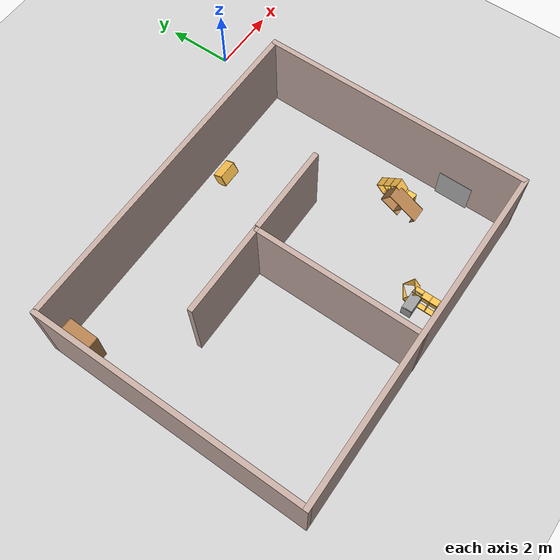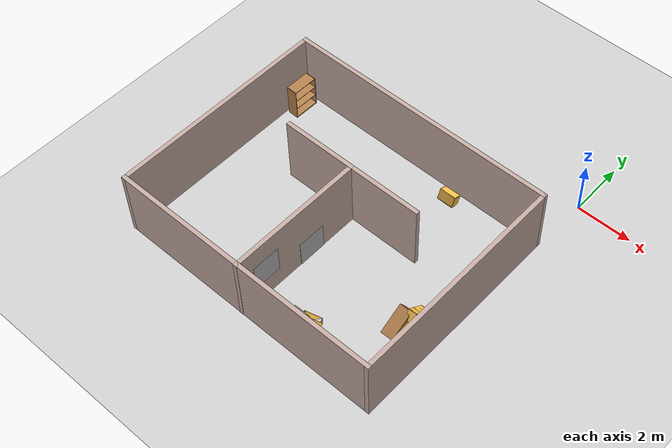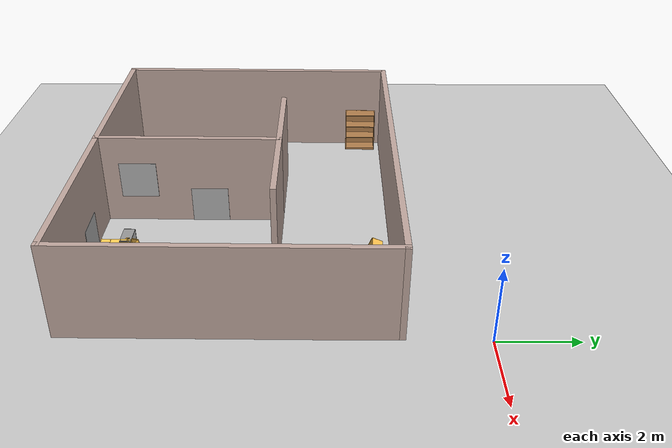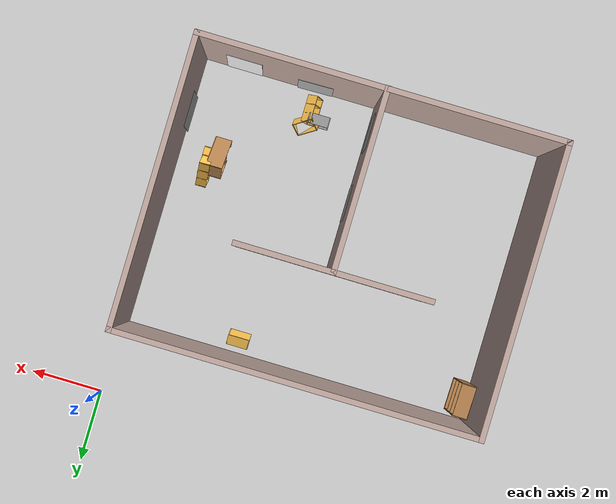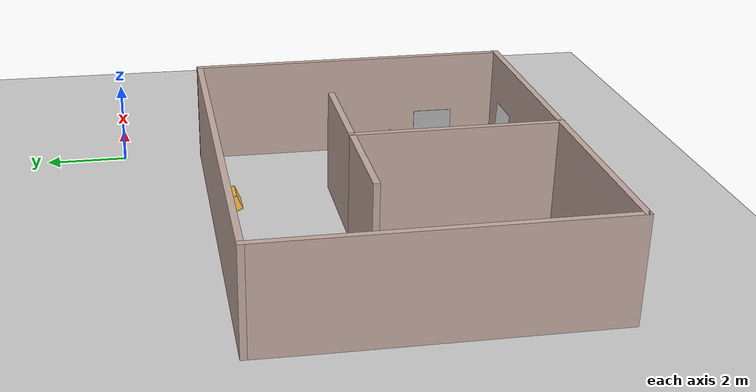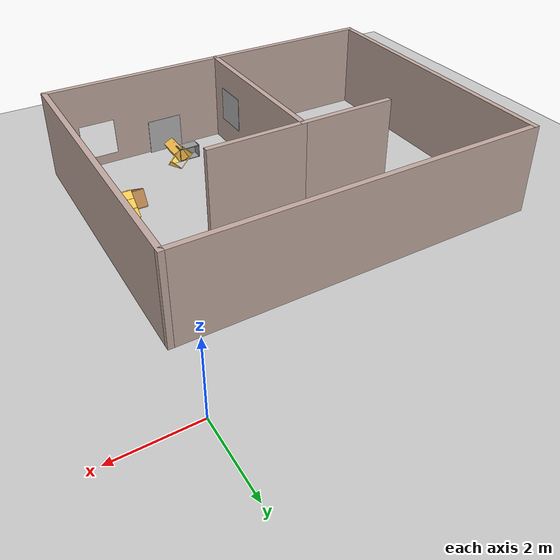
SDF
<sdf version="1.6">
 <world name="default">
  <light name="sun" type="directional">
   <pose>0 0 10 0 -0 0</pose>
   <diffuse>0.8 0.8 0.8 1</diffuse>
   <specular>0.1 0.1 0.1 1</specular>
   <attenuation>
    <range>1000</range>
    <constant>0.9</constant>
    <linear>0.01</linear>
    <quadratic>0.001</quadratic>
   </attenuation>
   <direction>-0.5 0.5 -1</direction>
  </light>
  <model name="ground_plane">
   <static>1</static>
   <link name="link">
    <collision name="collision">
     <geometry><plane><normal>0 0 1</normal><size>100 100</size></plane></geometry>
     <surface><friction><ode><mu>100</mu><mu2>50</mu2></ode></friction></surface>
    </collision>
    <visual name="visual">
     <cast_shadows>0</cast_shadows>
     <geometry><plane><normal>0 0 1</normal><size>100 100</size></plane></geometry>
     <material>
      <script><uri>file://media/materials/scripts/gazebo.material</uri><name>Gazebo/Grey</name></script>
     </material>
    </visual>
   </link>
  </model>
  <gravity>0 0 -9.8</gravity>
  <magnetic_field>6e-06 2.3e-05 -4.2e-05</magnetic_field>
  <atmosphere type="adiabatic"/>
  <physics name="default_physics" default="0" type="ode">
   <max_step_size>0.001</max_step_size>
   <real_time_factor>1</real_time_factor>
   <real_time_update_rate>1000</real_time_update_rate>
  </physics>
  <scene><ambient>0.4 0.4 0.4 1</ambient><background>0.7 0.7 0.7 1</background><shadows>1</shadows></scene>
  <spherical_coordinates>
   <surface_model>EARTH_WGS84</surface_model>
   <latitude_deg>0</latitude_deg>
   <longitude_deg>0</longitude_deg>
   <elevation>0</elevation>
   <heading_deg>0</heading_deg>
  </spherical_coordinates>
  <model name="empty_room_colored_walls">
   <pose>-5.06103 -5.97507 0 -0.005795 0 0</pose>
   <link name="Wall_62">
    <collision name="Wall_62_Collision">
     <geometry><box><size>10 0.15 2.5</size></box></geometry>
     <pose>0 0 1.25 0 -0 0</pose>
    </collision>
    <visual name="Wall_62_Visual">
     <pose>0 0 1.25 0 -0 0</pose>
     <geometry><box><size>10 0.15 2.5</size></box></geometry>
     <material>
      <script><uri>file://media/materials/scripts/gazebo.material</uri><name>Gazebo/Grey</name></script>
      <ambient>0.760784 0.662745 0.627451 1</ambient>
     </material>
    </visual>
    <pose>0 -3.92179 0 0 -0 0</pose>
   </link>
   <link name="Wall_63">
    <collision name="Wall_63_Collision">
     <geometry><box><size>8 0.15 2.5</size></box></geometry>
     <pose>0 0 1.25 0 -0 0</pose>
    </collision>
    <visual name="Wall_63_Visual">
     <pose>0 0 1.25 0 -0 0</pose>
     <geometry><box><size>8 0.15 2.5</size></box></geometry>
     <material>
      <script><uri>file://media/materials/scripts/gazebo.material</uri><name>Gazebo/Grey</name></script>
      <ambient>0.760784 0.662745 0.627451 1</ambient>
     </material>
    </visual>
    <pose>4.925 0.003206 0 0 -0 1.5708</pose>
   </link>
   <link name="Wall_64">
    <collision name="Wall_64_Collision">
     <geometry><box><size>10 0.15 2.5</size></box></geometry>
     <pose>0 0 1.25 0 -0 0</pose>
    </collision>
    <visual name="Wall_64_Visual">
     <pose>0 0 1.25 0 -0 0</pose>
     <geometry><box><size>10 0.15 2.5</size></box></geometry>
     <material>
      <script><uri>file://media/materials/scripts/gazebo.material</uri><name>Gazebo/Grey</name></script>
      <ambient>0.760784 0.662745 0.627451 1</ambient>
     </material>
    </visual>
    <pose>0 3.92821 0 0 -0 3.14159</pose>
   </link>
   <link name="Wall_65">
    <collision name="Wall_65_Collision">
     <geometry><box><size>8 0.15 2.5</size></box></geometry>
     <pose>0 0 1.25 0 -0 0</pose>
    </collision>
    <visual name="Wall_65_Visual">
     <pose>0 0 1.25 0 -0 0</pose>
     <geometry><box><size>8 0.15 2.5</size></box></geometry>
     <material>
      <script><uri>file://media/materials/scripts/gazebo.material</uri><name>Gazebo/Grey</name></script>
      <ambient>0.760784 0.662745 0.627451 1</ambient>
     </material>
    </visual>
    <pose>-4.925 0.003206 0 0 0 -1.5708</pose>
   </link>
   <link name="Wall_70">
    <collision name="Wall_70_Collision">
     <geometry><box><size>5 0.15 2.5</size></box></geometry>
     <pose>0 0 1.25 0 -0 0</pose>
    </collision>
    <visual name="Wall_70_Visual">
     <pose>0 0 1.25 0 -0 0</pose>
     <geometry><box><size>5 0.15 2.5</size></box></geometry>
     <material>
      <script><uri>file://media/materials/scripts/gazebo.material</uri><name>Gazebo/Grey</name></script>
      <ambient>0.760784 0.662745 0.627451 1</ambient>
     </material>
    </visual>
    <pose>-0.121943 -1.50321 0 0 -0 1.5708</pose>
   </link>
   <link name="Wall_71">
    <collision name="Wall_71_Collision">
     <geometry><box><size>2.75 0.15 2.5</size></box></geometry>
     <pose>0 0 1.25 0 -0 0</pose>
    </collision>
    <visual name="Wall_71_Visual">
     <pose>0 0 1.25 0 -0 0</pose>
     <geometry><box><size>2.75 0.15 2.5</size></box></geometry>
     <material>
      <script><uri>file://media/materials/scripts/gazebo.material</uri><name>Gazebo/Grey</name></script>
      <ambient>0.760784 0.662745 0.627451 1</ambient>
     </material>
    </visual>
    <pose>1.17806 0.921794 0 0 -0 0</pose>
   </link>
   <link name="Wall_73">
    <collision name="Wall_73_Collision">
     <geometry><box><size>2.75 0.15 2.5</size></box></geometry>
     <pose>0 0 1.25 0 -0 0</pose>
    </collision>
    <visual name="Wall_73_Visual">
     <pose>0 0 1.25 0 -0 0</pose>
     <geometry><box><size>2.75 0.15 2.5</size></box></geometry>
     <material>
      <script><uri>file://media/materials/scripts/gazebo.material</uri><name>Gazebo/Grey</name></script>
      <ambient>0.760784 0.662745 0.627451 1</ambient>
     </material>
    </visual>
    <pose>-1.42194 0.921794 0 0 -0 3.14159</pose>
   </link>
   <static>1</static>
  </model>
  <model name="bookshelf">
   <static>1</static>
   <link name="link">
    <inertial><mass>1</mass></inertial>
    <collision name="back">
     <pose>0 0.005 0.6 0 -0 0</pose>
     <geometry><box><size>0.9 0.01 1.2</size></box></geometry>
    </collision>
    <visual name="visual1">
     <pose>0 0.005 0.6 0 -0 0</pose>
     <geometry><box><size>0.9 0.01 1.2</size></box></geometry>
     <material>
      <script><uri>file://media/materials/scripts/gazebo.material</uri><name>Gazebo/Wood</name></script>
     </material>
    </visual>
    <collision name="left_side">
     <pose>0.45 -0.195 0.6 0 -0 0</pose>
     <geometry><box><size>0.02 0.4 1.2</size></box></geometry>
    </collision>
    <visual name="visual2">
     <pose>0.45 -0.195 0.6 0 -0 0</pose>
     <geometry><box><size>0.02 0.4 1.2</size></box></geometry>
     <material>
      <script><uri>file://media/materials/scripts/gazebo.material</uri><name>Gazebo/Wood</name></script>
     </material>
    </visual>
    <collision name="right_side">
     <pose>-0.45 -0.195 0.6 0 -0 0</pose>
     <geometry><box><size>0.02 0.4 1.2</size></box></geometry>
    </collision>
    <visual name="visual3">
     <pose>-0.45 -0.195 0.6 0 -0 0</pose>
     <geometry><box><size>0.02 0.4 1.2</size></box></geometry>
     <material>
      <script><uri>file://media/materials/scripts/gazebo.material</uri><name>Gazebo/Wood</name></script>
     </material>
    </visual>
    <collision name="bottom">
     <pose>0 -0.195 0.03 0 -0 0</pose>
     <geometry><box><size>0.88 0.4 0.06</size></box></geometry>
    </collision>
    <visual name="visual4">
     <pose>0 -0.195 0.03 0 -0 0</pose>
     <geometry><box><size>0.88 0.4 0.06</size></box></geometry>
     <material>
      <script><uri>file://media/materials/scripts/gazebo.material</uri><name>Gazebo/Wood</name></script>
     </material>
    </visual>
    <collision name="top">
     <pose>0 -0.195 1.19 0 -0 0</pose>
     <geometry><box><size>0.88 0.4 0.02</size></box></geometry>
    </collision>
    <visual name="visual5">
     <pose>0 -0.195 1.19 0 -0 0</pose>
     <geometry><box><size>0.88 0.4 0.02</size></box></geometry>
     <material>
      <script><uri>file://media/materials/scripts/gazebo.material</uri><name>Gazebo/Wood</name></script>
     </material>
    </visual>
    <collision name="low_shelf">
     <pose>0 -0.195 0.43 0 -0 0</pose>
     <geometry><box><size>0.88 0.4 0.02</size></box></geometry>
    </collision>
    <visual name="visual6">
     <pose>0 -0.195 0.43 0 -0 0</pose>
     <geometry><box><size>0.88 0.4 0.02</size></box></geometry>
     <material>
      <script><uri>file://media/materials/scripts/gazebo.material</uri><name>Gazebo/Wood</name></script>
     </material>
    </visual>
    <collision name="high_shelf">
     <pose>0 -0.195 0.8 0 -0 0</pose>
     <geometry><box><size>0.88 0.4 0.02</size></box></geometry>
    </collision>
    <visual name="visual7">
     <pose>0 -0.195 0.8 0 -0 0</pose>
     <geometry><box><size>0.88 0.4 0.02</size></box></geometry>
     <material>
      <script><uri>file://media/materials/scripts/gazebo.material</uri><name>Gazebo/Wood</name></script>
     </material>
    </visual>
   </link>
   <pose>-9.80012 -2.72902 0 0 -0 1.5503</pose>
  </model>
  <model name="Wall_Cabinet_24x15M">
   <link name="Wall_41">
    <pose>0 0 0.01 0 -0 0</pose>
    <inertial>
     <mass>1.4983</mass>
     <inertia><ixx>0.011</ixx><iyy>0.0571</iyy><izz>0.0462</izz><ixy>0</ixy><ixz>0</ixz><iyz>0</iyz></inertia>
    </inertial>
    <collision name="Wall_41_Collision"><geometry><box><size>0.608 0.296 0.02</size></box></geometry></collision>
    <visual name="Wall_41_Visual">
     <geometry><box><size>0.608 0.296 0.02</size></box></geometry>
     <material>
      <script><uri>file://media/materials/scripts/gazebo.material</uri><name>Gazebo/Grey</name></script>
      <ambient>1 0.764706 0.305882 1</ambient>
     </material>
    </visual>
    <pose>0.000184 0.181953 0 0 -0 0</pose>
   </link>
   <joint name="41_43" type="fixed">
    <pose>-0.304 0 0 0 -0 0</pose>
    <parent>Wall_43</parent>
    <child>Wall_41</child>
    <axis>
     <xyz>0 0 1</xyz>
     <use_parent_model_frame>0</use_parent_model_frame>
     <limit><lower>-1e+16</lower><upper>1e+16</upper></limit>
    </axis>
   </joint>
   <joint name="41_45" type="fixed">
    <pose>0.304 0 0 0 -0 0</pose>
    <parent>Wall_45</parent>
    <child>Wall_41</child>
    <axis>
     <xyz>0 0 1</xyz>
     <use_parent_model_frame>0</use_parent_model_frame>
     <limit><lower>-1e+16</lower><upper>1e+16</upper></limit>
    </axis>
   </joint>
   <joint name="41_49" type="fixed">
    <pose>0 -0.148 0 0 -0 0</pose>
    <parent>Wall_49</parent>
    <child>Wall_41</child>
    <axis>
     <xyz>0 0 1</xyz>
     <use_parent_model_frame>0</use_parent_model_frame>
     <limit><lower>-1e+16</lower><upper>1e+16</upper></limit>
    </axis>
   </joint>
   <link name="Wall_43">
    <pose>-0.294 0 0.192 0 -0 0</pose>
    <inertial>
     <mass>0.9463</mass>
     <inertia><ixx>0.0069</ixx><iyy>0.0185</iyy><izz>0.0117</izz><ixy>0</ixy><ixz>0</ixz><iyz>0</iyz></inertia>
    </inertial>
    <collision name="Wall_43_Collision"><geometry><box><size>0.02 0.296 0.384</size></box></geometry></collision>
    <visual name="Wall_43_Visual">
     <geometry><box><size>0.02 0.296 0.384</size></box></geometry>
     <material>
      <script><uri>file://media/materials/scripts/gazebo.material</uri><name>Gazebo/Grey</name></script>
      <ambient>1 0.764706 0.305882 1</ambient>
     </material>
    </visual>
   </link>
   <link name="Wall_45">
    <pose>0.294 0 0.192 0 -0 0</pose>
    <inertial>
     <mass>0.9463</mass>
     <inertia><ixx>0.0069</ixx><iyy>0.0185</iyy><izz>0.0117</izz><ixy>0</ixy><ixz>0</ixz><iyz>0</iyz></inertia>
    </inertial>
    <collision name="Wall_45_Collision"><geometry><box><size>0.02 0.296 0.384</size></box></geometry></collision>
    <visual name="Wall_45_Visual">
     <geometry><box><size>0.02 0.296 0.384</size></box></geometry>
     <material>
      <script><uri>file://media/materials/scripts/gazebo.material</uri><name>Gazebo/Grey</name></script>
      <ambient>1 0.764706 0.305882 1</ambient>
     </material>
    </visual>
   </link>
   <link name="Wall_47">
    <pose>0 0 0.374 0 -0 0</pose>
    <inertial>
     <mass>1.4983</mass>
     <inertia><ixx>0.011</ixx><iyy>0.0571</iyy><izz>0.0462</izz><ixy>0</ixy><ixz>0</ixz><iyz>0</iyz></inertia>
    </inertial>
    <collision name="Wall_47_Collision"><geometry><box><size>0.608 0.296 0.02</size></box></geometry></collision>
    <visual name="Wall_47_Visual">
     <geometry><box><size>0.608 0.296 0.02</size></box></geometry>
     <material>
      <script><uri>file://media/materials/scripts/gazebo.material</uri><name>Gazebo/Grey</name></script>
      <ambient>1 0.764706 0.305882 1</ambient>
     </material>
    </visual>
   </link>
   <joint name="47_43" type="fixed">
    <pose>-0.304 0 0 0 -0 0</pose>
    <parent>Wall_43</parent>
    <child>Wall_47</child>
    <axis>
     <xyz>0 0 1</xyz>
     <use_parent_model_frame>0</use_parent_model_frame>
     <limit><lower>-1e+16</lower><upper>1e+16</upper></limit>
    </axis>
   </joint>
   <joint name="47_45" type="fixed">
    <pose>0.304 0 0 0 -0 0</pose>
    <parent>Wall_45</parent>
    <child>Wall_47</child>
    <axis>
     <xyz>0 0 1</xyz>
     <use_parent_model_frame>0</use_parent_model_frame>
     <limit><lower>-1e+16</lower><upper>1e+16</upper></limit>
    </axis>
   </joint>
   <joint name="47_49" type="fixed">
    <pose>0 -0.148 0 0 -0 0</pose>
    <parent>Wall_49</parent>
    <child>Wall_47</child>
    <axis>
     <xyz>0 0 1</xyz>
     <use_parent_model_frame>0</use_parent_model_frame>
     <limit><lower>-1e+16</lower><upper>1e+16</upper></limit>
    </axis>
   </joint>
   <link name="Wall_49">
    <pose>0 -0.138 0.19 0 -0 0</pose>
    <inertial>
     <mass>1.9108</mass>
     <inertia><ixx>0.0231</ixx><iyy>0.0582</iyy><izz>0.0811</izz><ixy>0</ixy><ixz>0</ixz><iyz>0</iyz></inertia>
    </inertial>
    <collision name="Wall_49_Collision"><geometry><box><size>0.604 0.02 0.38</size></box></geometry></collision>
    <visual name="Wall_49_Visual">
     <geometry><box><size>0.604 0.02 0.38</size></box></geometry>
     <material>
      <script><uri>file://media/materials/scripts/gazebo.material</uri><name>Gazebo/Grey</name></script>
      <ambient>1 0.764706 0.305882 1</ambient>
     </material>
    </visual>
   </link>
   <joint name="49_43" type="fixed">
    <pose>-0.302 0 0 0 -0 0</pose>
    <parent>Wall_41</parent>
    <child>Wall_49</child>
    <axis>
     <xyz>0 1 0</xyz>
     <use_parent_model_frame>0</use_parent_model_frame>
     <limit><lower>-1e+16</lower><upper>1e+16</upper></limit>
    </axis>
   </joint>
   <joint name="49_45" type="fixed">
    <pose>0.302 0 0 0 -0 0</pose>
    <parent>Wall_45</parent>
    <child>Wall_49</child>
    <axis>
     <xyz>0 1 0</xyz>
     <use_parent_model_frame>0</use_parent_model_frame>
     <limit><lower>-1e+16</lower><upper>1e+16</upper></limit>
    </axis>
   </joint>
   <static>1</static>
   <pose>-3.30759 -2.60525 0 -0.417028 0 0</pose>
  </model>
  <model name="Wall_Cabinet_15x30_0">
   <pose>-1.03531 -7.03812 0 0 -0 0</pose>
   <link name="Wall_0">
    <pose>0 0.374 0.192 0 -0 0</pose>
    <inertial>
     <mass>0.9882</mass>
     <inertia><ixx>0.0072</ixx><iyy>0.0194</iyy><izz>0.0122</izz><ixy>0</ixy><ixz>0</ixz><iyz>0</iyz></inertia>
    </inertial>
    <collision name="Wall_0_Collision"><geometry><box><size>0.296 0.02 0.384</size></box></geometry></collision>
    <visual name="Wall_0_Visual">
     <geometry><box><size>0.296 0.02 0.384</size></box></geometry>
     <material>
      <script><uri>file://media/materials/scripts/gazebo.material</uri><name>Gazebo/Grey</name></script>
      <ambient>1 0.764706 0.305882 1</ambient>
     </material>
    </visual>
   </link>
   <joint name="0_2" type="fixed">
    <pose>0 0 0.192 0 -0 0</pose>
    <parent>Wall_2</parent>
    <child>Wall_0</child>
    <axis>
     <xyz>0 0 1</xyz>
     <use_parent_model_frame>0</use_parent_model_frame>
     <limit><lower>-1e+16</lower><upper>1e+16</upper></limit>
    </axis>
   </joint>
   <joint name="0_4" type="fixed">
    <pose>0 0 -0.192 0 -0 0</pose>
    <parent>Wall_4</parent>
    <child>Wall_0</child>
    <axis>
     <xyz>0 0 1</xyz>
     <use_parent_model_frame>0</use_parent_model_frame>
     <limit><lower>-1e+16</lower><upper>1e+16</upper></limit>
    </axis>
   </joint>
   <joint name="0_15" type="fixed">
    <pose>0.148 0 0 0 -0 0</pose>
    <parent>Wall_15</parent>
    <child>Wall_0</child>
    <axis>
     <xyz>1 0 0</xyz>
     <use_parent_model_frame>0</use_parent_model_frame>
     <limit><lower>-1e+16</lower><upper>1e+16</upper></limit>
    </axis>
   </joint>
   <link name="Wall_11">
    <pose>0 -0.132768 0.192 0 -0 0</pose>
    <inertial>
     <mass>0.9882</mass>
     <inertia><ixx>0.0072</ixx><iyy>0.0194</iyy><izz>0.0122</izz><ixy>0</ixy><ixz>0</ixz><iyz>0</iyz></inertia>
    </inertial>
    <collision name="Wall_11_Collision"><geometry><box><size>0.296 0.02 0.384</size></box></geometry></collision>
    <visual name="Wall_11_Visual">
     <geometry><box><size>0.296 0.02 0.384</size></box></geometry>
     <material>
      <script><uri>file://media/materials/scripts/gazebo.material</uri><name>Gazebo/Grey</name></script>
      <ambient>1 0.764706 0.305882 1</ambient>
     </material>
    </visual>
   </link>
   <joint name="11_2" type="fixed">
    <pose>0 0 0.192 0 -0 0</pose>
    <parent>Wall_2</parent>
    <child>Wall_11</child>
    <axis>
     <xyz>0 0 1</xyz>
     <use_parent_model_frame>0</use_parent_model_frame>
     <limit><lower>-1e+16</lower><upper>1e+16</upper></limit>
    </axis>
   </joint>
   <joint name="11_4" type="fixed">
    <pose>0 0 -0.192 0 -0 0</pose>
    <parent>Wall_4</parent>
    <child>Wall_11</child>
    <axis>
     <xyz>0 0 1</xyz>
     <use_parent_model_frame>0</use_parent_model_frame>
     <limit><lower>-1e+16</lower><upper>1e+16</upper></limit>
    </axis>
   </joint>
   <joint name="11_15" type="fixed">
    <pose>0.148 0 0 0 -0 0</pose>
    <parent>Wall_15</parent>
    <child>Wall_11</child>
    <axis>
     <xyz>1 0 0</xyz>
     <use_parent_model_frame>0</use_parent_model_frame>
     <limit><lower>-1e+16</lower><upper>1e+16</upper></limit>
    </axis>
   </joint>
   <link name="Wall_15">
    <pose>0.138 0 0.19 0 -0 0</pose>
    <inertial>
     <mass>2.5241</mass>
     <inertia><ixx>0.0305</ixx><iyy>0.1229</iyy><izz>0.1532</izz><ixy>0</ixy><ixz>0</ixz><iyz>0</iyz></inertia>
    </inertial>
    <collision name="Wall_15_Collision"><geometry><box><size>0.02 0.764 0.38</size></box></geometry></collision>
    <visual name="Wall_15_Visual">
     <geometry><box><size>0.02 0.764 0.38</size></box></geometry>
     <material>
      <script><uri>file://media/materials/scripts/gazebo.material</uri><name>Gazebo/Grey</name></script>
      <ambient>1 0.764706 0.305882 1</ambient>
     </material>
    </visual>
   </link>
   <joint name="15_2" type="fixed">
    <pose>0 0 0.19 0 -0 0</pose>
    <parent>Wall_2</parent>
    <child>Wall_15</child>
    <axis>
     <xyz>0 0 1</xyz>
     <use_parent_model_frame>0</use_parent_model_frame>
     <limit><lower>-1e+16</lower><upper>1e+16</upper></limit>
    </axis>
   </joint>
   <joint name="15_4" type="fixed">
    <pose>0 0 -0.19 0 -0 0</pose>
    <parent>Wall_4</parent>
    <child>Wall_15</child>
    <axis>
     <xyz>0 0 1</xyz>
     <use_parent_model_frame>0</use_parent_model_frame>
     <limit><lower>-1e+16</lower><upper>1e+16</upper></limit>
    </axis>
   </joint>
   <link name="Wall_2">
    <pose>0 0 0.374 0 -0 0</pose>
    <inertial>
     <mass>1.9765</mass>
     <inertia><ixx>0.0145</ixx><iyy>0.1116</iyy><izz>0.0972</izz><ixy>0</ixy><ixz>0</ixz><iyz>0</iyz></inertia>
    </inertial>
    <collision name="Wall_2_Collision"><geometry><box><size>0.296 0.768 0.02</size></box></geometry></collision>
    <visual name="Wall_2_Visual">
     <geometry><box><size>0.296 0.768 0.02</size></box></geometry>
     <material>
      <script><uri>file://media/materials/scripts/gazebo.material</uri><name>Gazebo/Grey</name></script>
      <ambient>1 0.764706 0.305882 1</ambient>
     </material>
    </visual>
   </link>
   <link name="Wall_4">
    <pose>0 0 0.01 0 -0 0</pose>
    <inertial>
     <mass>1.9765</mass>
     <inertia><ixx>0.0145</ixx><iyy>0.1116</iyy><izz>0.0972</izz><ixy>0</ixy><ixz>0</ixz><iyz>0</iyz></inertia>
    </inertial>
    <collision name="Wall_4_Collision"><geometry><box><size>0.296 0.768 0.02</size></box></geometry></collision>
    <visual name="Wall_4_Visual">
     <geometry><box><size>0.296 0.768 0.02</size></box></geometry>
     <material>
      <script><uri>file://media/materials/scripts/gazebo.material</uri><name>Gazebo/Grey</name></script>
      <ambient>1 0.764706 0.305882 1</ambient>
     </material>
    </visual>
    <pose>-0.181124 0 0 0 0 -1.5708</pose>
   </link>
   <link name="Wall_6">
    <pose>0 -0.374 0.192 0 -0 0</pose>
    <inertial>
     <mass>0.9882</mass>
     <inertia><ixx>0.0072</ixx><iyy>0.0194</iyy><izz>0.0122</izz><ixy>0</ixy><ixz>0</ixz><iyz>0</iyz></inertia>
    </inertial>
    <collision name="Wall_6_Collision"><geometry><box><size>0.296 0.02 0.384</size></box></geometry></collision>
    <visual name="Wall_6_Visual">
     <geometry><box><size>0.296 0.02 0.384</size></box></geometry>
     <material>
      <script><uri>file://media/materials/scripts/gazebo.material</uri><name>Gazebo/Grey</name></script>
      <ambient>1 0.764706 0.305882 1</ambient>
     </material>
    </visual>
   </link>
   <joint name="6_2" type="fixed">
    <pose>0 0 0.192 0 -0 0</pose>
    <parent>Wall_2</parent>
    <child>Wall_6</child>
    <axis>
     <xyz>0 0 1</xyz>
     <use_parent_model_frame>0</use_parent_model_frame>
     <limit><lower>-1e+16</lower><upper>1e+16</upper></limit>
    </axis>
   </joint>
   <joint name="6_4" type="fixed">
    <pose>0 0 -0.192 0 -0 0</pose>
    <parent>Wall_4</parent>
    <child>Wall_6</child>
    <axis>
     <xyz>0 0 1</xyz>
     <use_parent_model_frame>0</use_parent_model_frame>
     <limit><lower>-1e+16</lower><upper>1e+16</upper></limit>
    </axis>
   </joint>
   <joint name="6_15" type="fixed">
    <pose>0.148 0 0 0 -0 0</pose>
    <parent>Wall_15</parent>
    <child>Wall_6</child>
    <axis>
     <xyz>1 0 0</xyz>
     <use_parent_model_frame>0</use_parent_model_frame>
     <limit><lower>-1e+16</lower><upper>1e+16</upper></limit>
    </axis>
   </joint>
   <link name="Wall_8">
    <pose>0 0.120833 0.192 0 -0 0</pose>
    <inertial>
     <mass>0.9882</mass>
     <inertia><ixx>0.0072</ixx><iyy>0.0194</iyy><izz>0.0122</izz><ixy>0</ixy><ixz>0</ixz><iyz>0</iyz></inertia>
    </inertial>
    <collision name="Wall_8_Collision"><geometry><box><size>0.296 0.02 0.384</size></box></geometry></collision>
    <visual name="Wall_8_Visual">
     <geometry><box><size>0.296 0.02 0.384</size></box></geometry>
     <material>
      <script><uri>file://media/materials/scripts/gazebo.material</uri><name>Gazebo/Grey</name></script>
      <ambient>1 0.764706 0.305882 1</ambient>
     </material>
    </visual>
   </link>
   <joint name="8_2" type="fixed">
    <pose>0 0 0.192 0 -0 0</pose>
    <parent>Wall_2</parent>
    <child>Wall_8</child>
    <axis>
     <xyz>0 0 1</xyz>
     <use_parent_model_frame>0</use_parent_model_frame>
     <limit><lower>-1e+16</lower><upper>1e+16</upper></limit>
    </axis>
   </joint>
   <joint name="8_4" type="fixed">
    <pose>0 0 -0.192 0 -0 0</pose>
    <parent>Wall_4</parent>
    <child>Wall_8</child>
    <axis>
     <xyz>0 0 1</xyz>
     <use_parent_model_frame>0</use_parent_model_frame>
     <limit><lower>-1e+16</lower><upper>1e+16</upper></limit>
    </axis>
   </joint>
   <joint name="8_15" type="fixed">
    <pose>0.148 0 0 0 -0 0</pose>
    <parent>Wall_15</parent>
    <child>Wall_8</child>
    <axis>
     <xyz>1 0 0</xyz>
     <use_parent_model_frame>0</use_parent_model_frame>
     <limit><lower>-1e+16</lower><upper>1e+16</upper></limit>
    </axis>
   </joint>
   <static>1</static>
  </model>
  <model name="Wall_Cabinet_15x30_1">
   <pose>-1.0711 -6.85196 0.260684 -0.696878 0 0</pose>
   <link name="Wall_0">
    <pose>0 0.374 0.192 0 -0 0</pose>
    <inertial>
     <mass>0.9882</mass>
     <inertia><ixx>0.0072</ixx><iyy>0.0194</iyy><izz>0.0122</izz><ixy>0</ixy><ixz>0</ixz><iyz>0</iyz></inertia>
    </inertial>
    <collision name="Wall_0_Collision"><geometry><box><size>0.296 0.02 0.384</size></box></geometry></collision>
    <visual name="Wall_0_Visual">
     <geometry><box><size>0.296 0.02 0.384</size></box></geometry>
     <material>
      <script><uri>file://media/materials/scripts/gazebo.material</uri><name>Gazebo/Grey</name></script>
      <ambient>1 0.764706 0.305882 1</ambient>
     </material>
    </visual>
   </link>
   <joint name="0_2" type="fixed">
    <pose>0 0 0.192 0 -0 0</pose>
    <parent>Wall_2</parent>
    <child>Wall_0</child>
    <axis>
     <xyz>0 0 1</xyz>
     <use_parent_model_frame>0</use_parent_model_frame>
     <limit><lower>-1e+16</lower><upper>1e+16</upper></limit>
    </axis>
   </joint>
   <joint name="0_4" type="fixed">
    <pose>0 0 -0.192 0 -0 0</pose>
    <parent>Wall_4</parent>
    <child>Wall_0</child>
    <axis>
     <xyz>0 0 1</xyz>
     <use_parent_model_frame>0</use_parent_model_frame>
     <limit><lower>-1e+16</lower><upper>1e+16</upper></limit>
    </axis>
   </joint>
   <joint name="0_15" type="fixed">
    <pose>0.148 0 0 0 -0 0</pose>
    <parent>Wall_15</parent>
    <child>Wall_0</child>
    <axis>
     <xyz>1 0 0</xyz>
     <use_parent_model_frame>0</use_parent_model_frame>
     <limit><lower>-1e+16</lower><upper>1e+16</upper></limit>
    </axis>
   </joint>
   <link name="Wall_11">
    <pose>0 -0.132768 0.192 0 -0 0</pose>
    <inertial>
     <mass>0.9882</mass>
     <inertia><ixx>0.0072</ixx><iyy>0.0194</iyy><izz>0.0122</izz><ixy>0</ixy><ixz>0</ixz><iyz>0</iyz></inertia>
    </inertial>
    <collision name="Wall_11_Collision"><geometry><box><size>0.296 0.02 0.384</size></box></geometry></collision>
    <visual name="Wall_11_Visual">
     <geometry><box><size>0.296 0.02 0.384</size></box></geometry>
     <material>
      <script><uri>file://media/materials/scripts/gazebo.material</uri><name>Gazebo/Grey</name></script>
      <ambient>1 0.764706 0.305882 1</ambient>
     </material>
    </visual>
   </link>
   <joint name="11_2" type="fixed">
    <pose>0 0 0.192 0 -0 0</pose>
    <parent>Wall_2</parent>
    <child>Wall_11</child>
    <axis>
     <xyz>0 0 1</xyz>
     <use_parent_model_frame>0</use_parent_model_frame>
     <limit><lower>-1e+16</lower><upper>1e+16</upper></limit>
    </axis>
   </joint>
   <joint name="11_4" type="fixed">
    <pose>0 0 -0.192 0 -0 0</pose>
    <parent>Wall_4</parent>
    <child>Wall_11</child>
    <axis>
     <xyz>0 0 1</xyz>
     <use_parent_model_frame>0</use_parent_model_frame>
     <limit><lower>-1e+16</lower><upper>1e+16</upper></limit>
    </axis>
   </joint>
   <joint name="11_15" type="fixed">
    <pose>0.148 0 0 0 -0 0</pose>
    <parent>Wall_15</parent>
    <child>Wall_11</child>
    <axis>
     <xyz>1 0 0</xyz>
     <use_parent_model_frame>0</use_parent_model_frame>
     <limit><lower>-1e+16</lower><upper>1e+16</upper></limit>
    </axis>
   </joint>
   <link name="Wall_15">
    <pose>0.138 0 0.19 0 -0 0</pose>
    <inertial>
     <mass>2.5241</mass>
     <inertia><ixx>0.0305</ixx><iyy>0.1229</iyy><izz>0.1532</izz><ixy>0</ixy><ixz>0</ixz><iyz>0</iyz></inertia>
    </inertial>
    <collision name="Wall_15_Collision"><geometry><box><size>0.02 0.764 0.38</size></box></geometry></collision>
    <visual name="Wall_15_Visual">
     <geometry><box><size>0.02 0.764 0.38</size></box></geometry>
     <material>
      <script><uri>file://media/materials/scripts/gazebo.material</uri><name>Gazebo/Grey</name></script>
      <ambient>1 0.764706 0.305882 1</ambient>
     </material>
    </visual>
   </link>
   <joint name="15_2" type="fixed">
    <pose>0 0 0.19 0 -0 0</pose>
    <parent>Wall_2</parent>
    <child>Wall_15</child>
    <axis>
     <xyz>0 0 1</xyz>
     <use_parent_model_frame>0</use_parent_model_frame>
     <limit><lower>-1e+16</lower><upper>1e+16</upper></limit>
    </axis>
   </joint>
   <joint name="15_4" type="fixed">
    <pose>0 0 -0.19 0 -0 0</pose>
    <parent>Wall_4</parent>
    <child>Wall_15</child>
    <axis>
     <xyz>0 0 1</xyz>
     <use_parent_model_frame>0</use_parent_model_frame>
     <limit><lower>-1e+16</lower><upper>1e+16</upper></limit>
    </axis>
   </joint>
   <link name="Wall_2">
    <pose>0 0 0.374 0 -0 0</pose>
    <inertial>
     <mass>1.9765</mass>
     <inertia><ixx>0.0145</ixx><iyy>0.1116</iyy><izz>0.0972</izz><ixy>0</ixy><ixz>0</ixz><iyz>0</iyz></inertia>
    </inertial>
    <collision name="Wall_2_Collision"><geometry><box><size>0.296 0.768 0.02</size></box></geometry></collision>
    <visual name="Wall_2_Visual">
     <geometry><box><size>0.296 0.768 0.02</size></box></geometry>
     <material>
      <script><uri>file://media/materials/scripts/gazebo.material</uri><name>Gazebo/Grey</name></script>
      <ambient>1 0.764706 0.305882 1</ambient>
     </material>
    </visual>
   </link>
   <link name="Wall_4">
    <pose>0 0 0.01 0 -0 0</pose>
    <inertial>
     <mass>1.9765</mass>
     <inertia><ixx>0.0145</ixx><iyy>0.1116</iyy><izz>0.0972</izz><ixy>0</ixy><ixz>0</ixz><iyz>0</iyz></inertia>
    </inertial>
    <collision name="Wall_4_Collision"><geometry><box><size>0.296 0.768 0.02</size></box></geometry></collision>
    <visual name="Wall_4_Visual">
     <geometry><box><size>0.296 0.768 0.02</size></box></geometry>
     <material>
      <script><uri>file://media/materials/scripts/gazebo.material</uri><name>Gazebo/Grey</name></script>
      <ambient>1 0.764706 0.305882 1</ambient>
     </material>
    </visual>
    <pose>-0.181124 0 0 0 0 -1.5708</pose>
   </link>
   <link name="Wall_6">
    <pose>0 -0.374 0.192 0 -0 0</pose>
    <inertial>
     <mass>0.9882</mass>
     <inertia><ixx>0.0072</ixx><iyy>0.0194</iyy><izz>0.0122</izz><ixy>0</ixy><ixz>0</ixz><iyz>0</iyz></inertia>
    </inertial>
    <collision name="Wall_6_Collision"><geometry><box><size>0.296 0.02 0.384</size></box></geometry></collision>
    <visual name="Wall_6_Visual">
     <geometry><box><size>0.296 0.02 0.384</size></box></geometry>
     <material>
      <script><uri>file://media/materials/scripts/gazebo.material</uri><name>Gazebo/Grey</name></script>
      <ambient>1 0.764706 0.305882 1</ambient>
     </material>
    </visual>
   </link>
   <joint name="6_2" type="fixed">
    <pose>0 0 0.192 0 -0 0</pose>
    <parent>Wall_2</parent>
    <child>Wall_6</child>
    <axis>
     <xyz>0 0 1</xyz>
     <use_parent_model_frame>0</use_parent_model_frame>
     <limit><lower>-1e+16</lower><upper>1e+16</upper></limit>
    </axis>
   </joint>
   <joint name="6_4" type="fixed">
    <pose>0 0 -0.192 0 -0 0</pose>
    <parent>Wall_4</parent>
    <child>Wall_6</child>
    <axis>
     <xyz>0 0 1</xyz>
     <use_parent_model_frame>0</use_parent_model_frame>
     <limit><lower>-1e+16</lower><upper>1e+16</upper></limit>
    </axis>
   </joint>
   <joint name="6_15" type="fixed">
    <pose>0.148 0 0 0 -0 0</pose>
    <parent>Wall_15</parent>
    <child>Wall_6</child>
    <axis>
     <xyz>1 0 0</xyz>
     <use_parent_model_frame>0</use_parent_model_frame>
     <limit><lower>-1e+16</lower><upper>1e+16</upper></limit>
    </axis>
   </joint>
   <link name="Wall_8">
    <pose>0 0.120833 0.192 0 -0 0</pose>
    <inertial>
     <mass>0.9882</mass>
     <inertia><ixx>0.0072</ixx><iyy>0.0194</iyy><izz>0.0122</izz><ixy>0</ixy><ixz>0</ixz><iyz>0</iyz></inertia>
    </inertial>
    <collision name="Wall_8_Collision"><geometry><box><size>0.296 0.02 0.384</size></box></geometry></collision>
    <visual name="Wall_8_Visual">
     <geometry><box><size>0.296 0.02 0.384</size></box></geometry>
     <material>
      <script><uri>file://media/materials/scripts/gazebo.material</uri><name>Gazebo/Grey</name></script>
      <ambient>1 0.764706 0.305882 1</ambient>
     </material>
    </visual>
   </link>
   <joint name="8_2" type="fixed">
    <pose>0 0 0.192 0 -0 0</pose>
    <parent>Wall_2</parent>
    <child>Wall_8</child>
    <axis>
     <xyz>0 0 1</xyz>
     <use_parent_model_frame>0</use_parent_model_frame>
     <limit><lower>-1e+16</lower><upper>1e+16</upper></limit>
    </axis>
   </joint>
   <joint name="8_4" type="fixed">
    <pose>0 0 -0.192 0 -0 0</pose>
    <parent>Wall_4</parent>
    <child>Wall_8</child>
    <axis>
     <xyz>0 0 1</xyz>
     <use_parent_model_frame>0</use_parent_model_frame>
     <limit><lower>-1e+16</lower><upper>1e+16</upper></limit>
    </axis>
   </joint>
   <joint name="8_15" type="fixed">
    <pose>0.148 0 0 0 -0 0</pose>
    <parent>Wall_15</parent>
    <child>Wall_8</child>
    <axis>
     <xyz>1 0 0</xyz>
     <use_parent_model_frame>0</use_parent_model_frame>
     <limit><lower>-1e+16</lower><upper>1e+16</upper></limit>
    </axis>
   </joint>
   <static>1</static>
  </model>
  <model name="cabinet">
   <static>1</static>
   <link name="cabinet_bottom_plate">
    <inertial>
     <pose>0 0 -1 0 -0 0</pose>
     <inertia><ixx>2.05</ixx><ixy>0</ixy><ixz>0</ixz><iyy>2.05</iyy><iyz>0</iyz><izz>2.05</izz></inertia>
     <mass>25</mass>
    </inertial>
    <collision name="cabinet_bottom_plate_geom">
     <pose>0 0 0.01 0 -0 0</pose>
     <geometry><box><size>0.45 0.45 0.02</size></box></geometry>
    </collision>
    <visual name="cabinet_bottom_plate_geom_visual">
     <pose>0 0 0.01 0 -0 0</pose>
     <geometry><box><size>0.45 0.45 0.02</size></box></geometry>
     <material>
      <script><uri>file://media/materials/scripts/gazebo.material</uri><name>Gazebo/Wood</name></script>
     </material>
    </visual>
    <collision name="cabinet_bottom_plate_geom_cabinet_back_plate">
     <pose>0.235 0 0.51 0 -0 0</pose>
     <geometry><box><size>0.02 0.45 1.02</size></box></geometry>
    </collision>
    <visual name="cabinet_bottom_plate_geom_cabinet_back_plate_visual">
     <pose>0.235 0 0.51 0 -0 0</pose>
     <geometry><box><size>0.02 0.45 1.02</size></box></geometry>
     <material>
      <script><uri>file://media/materials/scripts/gazebo.material</uri><name>Gazebo/Wood</name></script>
     </material>
    </visual>
    <collision name="cabinet_bottom_plate_geom_cabinet_left_plate">
     <pose>0 0.235 0.51 0 -0 0</pose>
     <geometry><box><size>0.45 0.02 1.02</size></box></geometry>
    </collision>
    <visual name="cabinet_bottom_plate_geom_cabinet_left_plate_visual">
     <pose>0 0.235 0.51 0 -0 0</pose>
     <geometry><box><size>0.45 0.02 1.02</size></box></geometry>
     <material>
      <script><uri>file://media/materials/scripts/gazebo.material</uri><name>Gazebo/Wood</name></script>
     </material>
    </visual>
    <collision name="cabinet_bottom_plate_geom_cabinet_middle_plate">
     <pose>0 0 0.51 0 -0 0</pose>
     <geometry><box><size>0.45 0.45 0.02</size></box></geometry>
    </collision>
    <visual name="cabinet_bottom_plate_geom_cabinet_middle_plate_visual">
     <pose>0 0 0.51 0 -0 0</pose>
     <geometry><box><size>0.45 0.45 0.02</size></box></geometry>
     <material>
      <script><uri>file://media/materials/scripts/gazebo.material</uri><name>Gazebo/Wood</name></script>
     </material>
    </visual>
    <collision name="cabinet_bottom_plate_geom_cabinet_right_plate">
     <pose>0 -0.235 0.51 0 -0 0</pose>
     <geometry><box><size>0.45 0.02 1.02</size></box></geometry>
    </collision>
    <visual name="cabinet_bottom_plate_geom_cabinet_right_plate_visual">
     <pose>0 -0.235 0.51 0 -0 0</pose>
     <geometry><box><size>0.45 0.02 1.02</size></box></geometry>
     <material>
      <script><uri>file://media/materials/scripts/gazebo.material</uri><name>Gazebo/Wood</name></script>
     </material>
    </visual>
    <collision name="cabinet_bottom_plate_geom_cabinet_top_plate">
     <pose>0 0 1.01 0 -0 0</pose>
     <geometry><box><size>0.45 0.45 0.02</size></box></geometry>
    </collision>
    <visual name="cabinet_bottom_plate_geom_cabinet_top_plate_visual">
     <pose>0 0 1.01 0 -0 0</pose>
     <geometry><box><size>0.45 0.45 0.02</size></box></geometry>
     <material>
      <script><uri>file://media/materials/scripts/gazebo.material</uri><name>Gazebo/Wood</name></script>
     </material>
    </visual>
   </link>
   <pose>-1.32888 -7.66183 0 -1.03395 0 0</pose>
  </model>
  <model name="Wall_Cabinet_15x30_2">
   <pose>-3.54335 -9.24759 0 0 0.473353 0</pose>
   <link name="Wall_0">
    <pose>0 0.374 0.192 0 -0 0</pose>
    <inertial>
     <mass>0.9882</mass>
     <inertia><ixx>0.0072</ixx><iyy>0.0194</iyy><izz>0.0122</izz><ixy>0</ixy><ixz>0</ixz><iyz>0</iyz></inertia>
    </inertial>
    <collision name="Wall_0_Collision"><geometry><box><size>0.296 0.02 0.384</size></box></geometry></collision>
    <visual name="Wall_0_Visual">
     <geometry><box><size>0.296 0.02 0.384</size></box></geometry>
     <material>
      <script><uri>file://media/materials/scripts/gazebo.material</uri><name>Gazebo/Grey</name></script>
      <ambient>1 0.764706 0.305882 1</ambient>
     </material>
    </visual>
   </link>
   <joint name="0_2" type="fixed">
    <pose>0 0 0.192 0 -0 0</pose>
    <parent>Wall_2</parent>
    <child>Wall_0</child>
    <axis>
     <xyz>0 0 1</xyz>
     <use_parent_model_frame>0</use_parent_model_frame>
     <limit><lower>-1e+16</lower><upper>1e+16</upper></limit>
    </axis>
   </joint>
   <joint name="0_4" type="fixed">
    <pose>0 0 -0.192 0 -0 0</pose>
    <parent>Wall_4</parent>
    <child>Wall_0</child>
    <axis>
     <xyz>0 0 1</xyz>
     <use_parent_model_frame>0</use_parent_model_frame>
     <limit><lower>-1e+16</lower><upper>1e+16</upper></limit>
    </axis>
   </joint>
   <joint name="0_15" type="fixed">
    <pose>0.148 0 0 0 -0 0</pose>
    <parent>Wall_15</parent>
    <child>Wall_0</child>
    <axis>
     <xyz>1 0 0</xyz>
     <use_parent_model_frame>0</use_parent_model_frame>
     <limit><lower>-1e+16</lower><upper>1e+16</upper></limit>
    </axis>
   </joint>
   <link name="Wall_11">
    <pose>0 -0.132768 0.192 0 -0 0</pose>
    <inertial>
     <mass>0.9882</mass>
     <inertia><ixx>0.0072</ixx><iyy>0.0194</iyy><izz>0.0122</izz><ixy>0</ixy><ixz>0</ixz><iyz>0</iyz></inertia>
    </inertial>
    <collision name="Wall_11_Collision"><geometry><box><size>0.296 0.02 0.384</size></box></geometry></collision>
    <visual name="Wall_11_Visual">
     <geometry><box><size>0.296 0.02 0.384</size></box></geometry>
     <material>
      <script><uri>file://media/materials/scripts/gazebo.material</uri><name>Gazebo/Grey</name></script>
      <ambient>1 0.764706 0.305882 1</ambient>
     </material>
    </visual>
   </link>
   <joint name="11_2" type="fixed">
    <pose>0 0 0.192 0 -0 0</pose>
    <parent>Wall_2</parent>
    <child>Wall_11</child>
    <axis>
     <xyz>0 0 1</xyz>
     <use_parent_model_frame>0</use_parent_model_frame>
     <limit><lower>-1e+16</lower><upper>1e+16</upper></limit>
    </axis>
   </joint>
   <joint name="11_4" type="fixed">
    <pose>0 0 -0.192 0 -0 0</pose>
    <parent>Wall_4</parent>
    <child>Wall_11</child>
    <axis>
     <xyz>0 0 1</xyz>
     <use_parent_model_frame>0</use_parent_model_frame>
     <limit><lower>-1e+16</lower><upper>1e+16</upper></limit>
    </axis>
   </joint>
   <joint name="11_15" type="fixed">
    <pose>0.148 0 0 0 -0 0</pose>
    <parent>Wall_15</parent>
    <child>Wall_11</child>
    <axis>
     <xyz>1 0 0</xyz>
     <use_parent_model_frame>0</use_parent_model_frame>
     <limit><lower>-1e+16</lower><upper>1e+16</upper></limit>
    </axis>
   </joint>
   <link name="Wall_15">
    <pose>0.138 0 0.19 0 -0 0</pose>
    <inertial>
     <mass>2.5241</mass>
     <inertia><ixx>0.0305</ixx><iyy>0.1229</iyy><izz>0.1532</izz><ixy>0</ixy><ixz>0</ixz><iyz>0</iyz></inertia>
    </inertial>
    <collision name="Wall_15_Collision"><geometry><box><size>0.02 0.764 0.38</size></box></geometry></collision>
    <visual name="Wall_15_Visual">
     <geometry><box><size>0.02 0.764 0.38</size></box></geometry>
     <material>
      <script><uri>file://media/materials/scripts/gazebo.material</uri><name>Gazebo/Grey</name></script>
      <ambient>1 0.764706 0.305882 1</ambient>
     </material>
    </visual>
   </link>
   <joint name="15_2" type="fixed">
    <pose>0 0 0.19 0 -0 0</pose>
    <parent>Wall_2</parent>
    <child>Wall_15</child>
    <axis>
     <xyz>0 0 1</xyz>
     <use_parent_model_frame>0</use_parent_model_frame>
     <limit><lower>-1e+16</lower><upper>1e+16</upper></limit>
    </axis>
   </joint>
   <joint name="15_4" type="fixed">
    <pose>0 0 -0.19 0 -0 0</pose>
    <parent>Wall_4</parent>
    <child>Wall_15</child>
    <axis>
     <xyz>0 0 1</xyz>
     <use_parent_model_frame>0</use_parent_model_frame>
     <limit><lower>-1e+16</lower><upper>1e+16</upper></limit>
    </axis>
   </joint>
   <link name="Wall_2">
    <pose>0 0 0.374 0 -0 0</pose>
    <inertial>
     <mass>1.9765</mass>
     <inertia><ixx>0.0145</ixx><iyy>0.1116</iyy><izz>0.0972</izz><ixy>0</ixy><ixz>0</ixz><iyz>0</iyz></inertia>
    </inertial>
    <collision name="Wall_2_Collision"><geometry><box><size>0.296 0.768 0.02</size></box></geometry></collision>
    <visual name="Wall_2_Visual">
     <geometry><box><size>0.296 0.768 0.02</size></box></geometry>
     <material>
      <script><uri>file://media/materials/scripts/gazebo.material</uri><name>Gazebo/Grey</name></script>
      <ambient>1 0.764706 0.305882 1</ambient>
     </material>
    </visual>
   </link>
   <link name="Wall_4">
    <pose>0 0 0.01 0 -0 0</pose>
    <inertial>
     <mass>1.9765</mass>
     <inertia><ixx>0.0145</ixx><iyy>0.1116</iyy><izz>0.0972</izz><ixy>0</ixy><ixz>0</ixz><iyz>0</iyz></inertia>
    </inertial>
    <collision name="Wall_4_Collision"><geometry><box><size>0.296 0.768 0.02</size></box></geometry></collision>
    <visual name="Wall_4_Visual">
     <geometry><box><size>0.296 0.768 0.02</size></box></geometry>
     <material>
      <script><uri>file://media/materials/scripts/gazebo.material</uri><name>Gazebo/Grey</name></script>
      <ambient>1 0.764706 0.305882 1</ambient>
     </material>
    </visual>
    <pose>-0.181124 0 0 0 0 -1.5708</pose>
   </link>
   <link name="Wall_6">
    <pose>0 -0.374 0.192 0 -0 0</pose>
    <inertial>
     <mass>0.9882</mass>
     <inertia><ixx>0.0072</ixx><iyy>0.0194</iyy><izz>0.0122</izz><ixy>0</ixy><ixz>0</ixz><iyz>0</iyz></inertia>
    </inertial>
    <collision name="Wall_6_Collision"><geometry><box><size>0.296 0.02 0.384</size></box></geometry></collision>
    <visual name="Wall_6_Visual">
     <geometry><box><size>0.296 0.02 0.384</size></box></geometry>
     <material>
      <script><uri>file://media/materials/scripts/gazebo.material</uri><name>Gazebo/Grey</name></script>
      <ambient>1 0.764706 0.305882 1</ambient>
     </material>
    </visual>
   </link>
   <joint name="6_2" type="fixed">
    <pose>0 0 0.192 0 -0 0</pose>
    <parent>Wall_2</parent>
    <child>Wall_6</child>
    <axis>
     <xyz>0 0 1</xyz>
     <use_parent_model_frame>0</use_parent_model_frame>
     <limit><lower>-1e+16</lower><upper>1e+16</upper></limit>
    </axis>
   </joint>
   <joint name="6_4" type="fixed">
    <pose>0 0 -0.192 0 -0 0</pose>
    <parent>Wall_4</parent>
    <child>Wall_6</child>
    <axis>
     <xyz>0 0 1</xyz>
     <use_parent_model_frame>0</use_parent_model_frame>
     <limit><lower>-1e+16</lower><upper>1e+16</upper></limit>
    </axis>
   </joint>
   <joint name="6_15" type="fixed">
    <pose>0.148 0 0 0 -0 0</pose>
    <parent>Wall_15</parent>
    <child>Wall_6</child>
    <axis>
     <xyz>1 0 0</xyz>
     <use_parent_model_frame>0</use_parent_model_frame>
     <limit><lower>-1e+16</lower><upper>1e+16</upper></limit>
    </axis>
   </joint>
   <link name="Wall_8">
    <pose>0 0.120833 0.192 0 -0 0</pose>
    <inertial>
     <mass>0.9882</mass>
     <inertia><ixx>0.0072</ixx><iyy>0.0194</iyy><izz>0.0122</izz><ixy>0</ixy><ixz>0</ixz><iyz>0</iyz></inertia>
    </inertial>
    <collision name="Wall_8_Collision"><geometry><box><size>0.296 0.02 0.384</size></box></geometry></collision>
    <visual name="Wall_8_Visual">
     <geometry><box><size>0.296 0.02 0.384</size></box></geometry>
     <material>
      <script><uri>file://media/materials/scripts/gazebo.material</uri><name>Gazebo/Grey</name></script>
      <ambient>1 0.764706 0.305882 1</ambient>
     </material>
    </visual>
   </link>
   <joint name="8_2" type="fixed">
    <pose>0 0 0.192 0 -0 0</pose>
    <parent>Wall_2</parent>
    <child>Wall_8</child>
    <axis>
     <xyz>0 0 1</xyz>
     <use_parent_model_frame>0</use_parent_model_frame>
     <limit><lower>-1e+16</lower><upper>1e+16</upper></limit>
    </axis>
   </joint>
   <joint name="8_4" type="fixed">
    <pose>0 0 -0.192 0 -0 0</pose>
    <parent>Wall_4</parent>
    <child>Wall_8</child>
    <axis>
     <xyz>0 0 1</xyz>
     <use_parent_model_frame>0</use_parent_model_frame>
     <limit><lower>-1e+16</lower><upper>1e+16</upper></limit>
    </axis>
   </joint>
   <joint name="8_15" type="fixed">
    <pose>0.148 0 0 0 -0 0</pose>
    <parent>Wall_15</parent>
    <child>Wall_8</child>
    <axis>
     <xyz>1 0 0</xyz>
     <use_parent_model_frame>0</use_parent_model_frame>
     <limit><lower>-1e+16</lower><upper>1e+16</upper></limit>
    </axis>
   </joint>
   <static>1</static>
  </model>
  <model name="Wall_Cabinet_24x15M_0">
   <link name="Wall_41">
    <pose>0 0 0.01 0 -0 0</pose>
    <inertial>
     <mass>1.4983</mass>
     <inertia><ixx>0.011</ixx><iyy>0.0571</iyy><izz>0.0462</izz><ixy>0</ixy><ixz>0</ixz><iyz>0</iyz></inertia>
    </inertial>
    <collision name="Wall_41_Collision"><geometry><box><size>0.608 0.296 0.02</size></box></geometry></collision>
    <visual name="Wall_41_Visual">
     <geometry><box><size>0.608 0.296 0.02</size></box></geometry>
     <material>
      <script><uri>file://media/materials/scripts/gazebo.material</uri><name>Gazebo/Grey</name></script>
      <ambient>1 0.764706 0.305882 1</ambient>
     </material>
    </visual>
    <pose>0.000184 0.181953 0 0 -0 0</pose>
   </link>
   <joint name="41_43" type="fixed">
    <pose>-0.304 0 0 0 -0 0</pose>
    <parent>Wall_43</parent>
    <child>Wall_41</child>
    <axis>
     <xyz>0 0 1</xyz>
     <use_parent_model_frame>0</use_parent_model_frame>
     <limit><lower>-1e+16</lower><upper>1e+16</upper></limit>
    </axis>
   </joint>
   <joint name="41_45" type="fixed">
    <pose>0.304 0 0 0 -0 0</pose>
    <parent>Wall_45</parent>
    <child>Wall_41</child>
    <axis>
     <xyz>0 0 1</xyz>
     <use_parent_model_frame>0</use_parent_model_frame>
     <limit><lower>-1e+16</lower><upper>1e+16</upper></limit>
    </axis>
   </joint>
   <joint name="41_49" type="fixed">
    <pose>0 -0.148 0 0 -0 0</pose>
    <parent>Wall_49</parent>
    <child>Wall_41</child>
    <axis>
     <xyz>0 0 1</xyz>
     <use_parent_model_frame>0</use_parent_model_frame>
     <limit><lower>-1e+16</lower><upper>1e+16</upper></limit>
    </axis>
   </joint>
   <link name="Wall_43">
    <pose>-0.294 0 0.192 0 -0 0</pose>
    <inertial>
     <mass>0.9463</mass>
     <inertia><ixx>0.0069</ixx><iyy>0.0185</iyy><izz>0.0117</izz><ixy>0</ixy><ixz>0</ixz><iyz>0</iyz></inertia>
    </inertial>
    <collision name="Wall_43_Collision"><geometry><box><size>0.02 0.296 0.384</size></box></geometry></collision>
    <visual name="Wall_43_Visual">
     <geometry><box><size>0.02 0.296 0.384</size></box></geometry>
     <material>
      <script><uri>file://media/materials/scripts/gazebo.material</uri><name>Gazebo/Grey</name></script>
      <ambient>1 0.764706 0.305882 1</ambient>
     </material>
    </visual>
   </link>
   <link name="Wall_45">
    <pose>0.294 0 0.192 0 -0 0</pose>
    <inertial>
     <mass>0.9463</mass>
     <inertia><ixx>0.0069</ixx><iyy>0.0185</iyy><izz>0.0117</izz><ixy>0</ixy><ixz>0</ixz><iyz>0</iyz></inertia>
    </inertial>
    <collision name="Wall_45_Collision"><geometry><box><size>0.02 0.296 0.384</size></box></geometry></collision>
    <visual name="Wall_45_Visual">
     <geometry><box><size>0.02 0.296 0.384</size></box></geometry>
     <material>
      <script><uri>file://media/materials/scripts/gazebo.material</uri><name>Gazebo/Grey</name></script>
      <ambient>1 0.764706 0.305882 1</ambient>
     </material>
    </visual>
   </link>
   <link name="Wall_47">
    <pose>0 0 0.374 0 -0 0</pose>
    <inertial>
     <mass>1.4983</mass>
     <inertia><ixx>0.011</ixx><iyy>0.0571</iyy><izz>0.0462</izz><ixy>0</ixy><ixz>0</ixz><iyz>0</iyz></inertia>
    </inertial>
    <collision name="Wall_47_Collision"><geometry><box><size>0.608 0.296 0.02</size></box></geometry></collision>
    <visual name="Wall_47_Visual">
     <geometry><box><size>0.608 0.296 0.02</size></box></geometry>
     <material>
      <script><uri>file://media/materials/scripts/gazebo.material</uri><name>Gazebo/Grey</name></script>
      <ambient>1 0.764706 0.305882 1</ambient>
     </material>
    </visual>
   </link>
   <joint name="47_43" type="fixed">
    <pose>-0.304 0 0 0 -0 0</pose>
    <parent>Wall_43</parent>
    <child>Wall_47</child>
    <axis>
     <xyz>0 0 1</xyz>
     <use_parent_model_frame>0</use_parent_model_frame>
     <limit><lower>-1e+16</lower><upper>1e+16</upper></limit>
    </axis>
   </joint>
   <joint name="47_45" type="fixed">
    <pose>0.304 0 0 0 -0 0</pose>
    <parent>Wall_45</parent>
    <child>Wall_47</child>
    <axis>
     <xyz>0 0 1</xyz>
     <use_parent_model_frame>0</use_parent_model_frame>
     <limit><lower>-1e+16</lower><upper>1e+16</upper></limit>
    </axis>
   </joint>
   <joint name="47_49" type="fixed">
    <pose>0 -0.148 0 0 -0 0</pose>
    <parent>Wall_49</parent>
    <child>Wall_47</child>
    <axis>
     <xyz>0 0 1</xyz>
     <use_parent_model_frame>0</use_parent_model_frame>
     <limit><lower>-1e+16</lower><upper>1e+16</upper></limit>
    </axis>
   </joint>
   <link name="Wall_49">
    <pose>0 -0.138 0.19 0 -0 0</pose>
    <inertial>
     <mass>1.9108</mass>
     <inertia><ixx>0.0231</ixx><iyy>0.0582</iyy><izz>0.0811</izz><ixy>0</ixy><ixz>0</ixz><iyz>0</iyz></inertia>
    </inertial>
    <collision name="Wall_49_Collision"><geometry><box><size>0.604 0.02 0.38</size></box></geometry></collision>
    <visual name="Wall_49_Visual">
     <geometry><box><size>0.604 0.02 0.38</size></box></geometry>
     <material>
      <script><uri>file://media/materials/scripts/gazebo.material</uri><name>Gazebo/Grey</name></script>
      <ambient>1 0.764706 0.305882 1</ambient>
     </material>
    </visual>
   </link>
   <joint name="49_43" type="fixed">
    <pose>-0.302 0 0 0 -0 0</pose>
    <parent>Wall_41</parent>
    <child>Wall_49</child>
    <axis>
     <xyz>0 1 0</xyz>
     <use_parent_model_frame>0</use_parent_model_frame>
     <limit><lower>-1e+16</lower><upper>1e+16</upper></limit>
    </axis>
   </joint>
   <joint name="49_45" type="fixed">
    <pose>0.302 0 0 0 -0 0</pose>
    <parent>Wall_45</parent>
    <child>Wall_49</child>
    <axis>
     <xyz>0 1 0</xyz>
     <use_parent_model_frame>0</use_parent_model_frame>
     <limit><lower>-1e+16</lower><upper>1e+16</upper></limit>
    </axis>
   </joint>
   <static>1</static>
   <pose>-3.51303 -8.70948 0 0.929942 0.424853 0.504855</pose>
  </model>
  <model name="Wall_Cabinet_24x15W">
   <link name="Wall_41">
    <pose>0 0 0.01 0 -0 0</pose>
    <inertial>
     <mass>1.4983</mass>
     <inertia><ixx>0.011</ixx><iyy>0.0571</iyy><izz>0.0462</izz><ixy>0</ixy><ixz>0</ixz><iyz>0</iyz></inertia>
    </inertial>
    <collision name="Wall_41_Collision"><geometry><box><size>0.608 0.296 0.02</size></box></geometry></collision>
    <visual name="Wall_41_Visual">
     <geometry><box><size>0.608 0.296 0.02</size></box></geometry>
     <material>
      <script><uri>file://media/materials/scripts/gazebo.material</uri><name>Gazebo/Grey</name></script>
      <ambient>1 1 1 1</ambient>
     </material>
    </visual>
    <pose>0.000184 0.181953 0 0 -0 0</pose>
   </link>
   <joint name="41_43" type="fixed">
    <pose>-0.304 0 0 0 -0 0</pose>
    <parent>Wall_43</parent>
    <child>Wall_41</child>
    <axis>
     <xyz>0 0 1</xyz>
     <use_parent_model_frame>0</use_parent_model_frame>
     <limit><lower>-1e+16</lower><upper>1e+16</upper></limit>
    </axis>
   </joint>
   <joint name="41_45" type="fixed">
    <pose>0.304 0 0 0 -0 0</pose>
    <parent>Wall_45</parent>
    <child>Wall_41</child>
    <axis>
     <xyz>0 0 1</xyz>
     <use_parent_model_frame>0</use_parent_model_frame>
     <limit><lower>-1e+16</lower><upper>1e+16</upper></limit>
    </axis>
   </joint>
   <joint name="41_49" type="fixed">
    <pose>0 -0.148 0 0 -0 0</pose>
    <parent>Wall_49</parent>
    <child>Wall_41</child>
    <axis>
     <xyz>0 0 1</xyz>
     <use_parent_model_frame>0</use_parent_model_frame>
     <limit><lower>-1e+16</lower><upper>1e+16</upper></limit>
    </axis>
   </joint>
   <link name="Wall_43">
    <pose>-0.294 0 0.192 0 -0 0</pose>
    <inertial>
     <mass>0.9463</mass>
     <inertia><ixx>0.0069</ixx><iyy>0.0185</iyy><izz>0.0117</izz><ixy>0</ixy><ixz>0</ixz><iyz>0</iyz></inertia>
    </inertial>
    <collision name="Wall_43_Collision"><geometry><box><size>0.02 0.296 0.384</size></box></geometry></collision>
    <visual name="Wall_43_Visual">
     <geometry><box><size>0.02 0.296 0.384</size></box></geometry>
     <material>
      <script><uri>file://media/materials/scripts/gazebo.material</uri><name>Gazebo/Grey</name></script>
      <ambient>1 1 1 1</ambient>
     </material>
    </visual>
   </link>
   <link name="Wall_45">
    <pose>0.294 0 0.192 0 -0 0</pose>
    <inertial>
     <mass>0.9463</mass>
     <inertia><ixx>0.0069</ixx><iyy>0.0185</iyy><izz>0.0117</izz><ixy>0</ixy><ixz>0</ixz><iyz>0</iyz></inertia>
    </inertial>
    <collision name="Wall_45_Collision"><geometry><box><size>0.02 0.296 0.384</size></box></geometry></collision>
    <visual name="Wall_45_Visual">
     <geometry><box><size>0.02 0.296 0.384</size></box></geometry>
     <material>
      <script><uri>file://media/materials/scripts/gazebo.material</uri><name>Gazebo/Grey</name></script>
      <ambient>1 1 1 1</ambient>
     </material>
    </visual>
   </link>
   <link name="Wall_47">
    <pose>0 0 0.374 0 -0 0</pose>
    <inertial>
     <mass>1.4983</mass>
     <inertia><ixx>0.011</ixx><iyy>0.0571</iyy><izz>0.0462</izz><ixy>0</ixy><ixz>0</ixz><iyz>0</iyz></inertia>
    </inertial>
    <collision name="Wall_47_Collision"><geometry><box><size>0.608 0.296 0.02</size></box></geometry></collision>
    <visual name="Wall_47_Visual">
     <geometry><box><size>0.608 0.296 0.02</size></box></geometry>
     <material>
      <script><uri>file://media/materials/scripts/gazebo.material</uri><name>Gazebo/Grey</name></script>
      <ambient>1 1 1 1</ambient>
     </material>
    </visual>
   </link>
   <joint name="47_43" type="fixed">
    <pose>-0.304 0 0 0 -0 0</pose>
    <parent>Wall_43</parent>
    <child>Wall_47</child>
    <axis>
     <xyz>0 0 1</xyz>
     <use_parent_model_frame>0</use_parent_model_frame>
     <limit><lower>-1e+16</lower><upper>1e+16</upper></limit>
    </axis>
   </joint>
   <joint name="47_45" type="fixed">
    <pose>0.304 0 0 0 -0 0</pose>
    <parent>Wall_45</parent>
    <child>Wall_47</child>
    <axis>
     <xyz>0 0 1</xyz>
     <use_parent_model_frame>0</use_parent_model_frame>
     <limit><lower>-1e+16</lower><upper>1e+16</upper></limit>
    </axis>
   </joint>
   <joint name="47_49" type="fixed">
    <pose>0 -0.148 0 0 -0 0</pose>
    <parent>Wall_49</parent>
    <child>Wall_47</child>
    <axis>
     <xyz>0 0 1</xyz>
     <use_parent_model_frame>0</use_parent_model_frame>
     <limit><lower>-1e+16</lower><upper>1e+16</upper></limit>
    </axis>
   </joint>
   <link name="Wall_49">
    <pose>0 -0.138 0.19 0 -0 0</pose>
    <inertial>
     <mass>1.9108</mass>
     <inertia><ixx>0.0231</ixx><iyy>0.0582</iyy><izz>0.0811</izz><ixy>0</ixy><ixz>0</ixz><iyz>0</iyz></inertia>
    </inertial>
    <collision name="Wall_49_Collision"><geometry><box><size>0.604 0.02 0.38</size></box></geometry></collision>
    <visual name="Wall_49_Visual">
     <geometry><box><size>0.604 0.02 0.38</size></box></geometry>
     <material>
      <script><uri>file://media/materials/scripts/gazebo.material</uri><name>Gazebo/Grey</name></script>
      <ambient>1 1 1 1</ambient>
     </material>
    </visual>
   </link>
   <joint name="49_43" type="fixed">
    <pose>-0.302 0 0 0 -0 0</pose>
    <parent>Wall_41</parent>
    <child>Wall_49</child>
    <axis>
     <xyz>0 1 0</xyz>
     <use_parent_model_frame>0</use_parent_model_frame>
     <limit><lower>-1e+16</lower><upper>1e+16</upper></limit>
    </axis>
   </joint>
   <joint name="49_45" type="fixed">
    <pose>0.302 0 0 0 -0 0</pose>
    <parent>Wall_45</parent>
    <child>Wall_49</child>
    <axis>
     <xyz>0 1 0</xyz>
     <use_parent_model_frame>0</use_parent_model_frame>
     <limit><lower>-1e+16</lower><upper>1e+16</upper></limit>
    </axis>
   </joint>
   <static>1</static>
   <pose>-3.71654 -9.00302 0 0 -0 0</pose>
  </model>
  <model name="electric_plug_1_N">
   <link name="link_0">
    <pose>4e-06 0 0 0 -0 0</pose>
    <inertial>
     <mass>1</mass>
     <inertia>
      <ixx>0.166667</ixx>
      <ixy>0</ixy>
      <ixz>0</ixz>
      <iyy>0.166667</iyy>
      <iyz>0</iyz>
      <izz>0.166667</izz>
     </inertia>
    </inertial>
    <visual name="visual">
     <geometry><box><size>0.01 1 1</size></box></geometry>
     <material>
      <lighting>1</lighting>
      <script>
       <uri>model://electric_plug_1_N/materials/scripts</uri>
       <uri>model://electric_plug_1_N/materials/textures</uri>
       <name>Electric/Plug1N</name>
      </script>
      <ambient>0.3 0.3 0.3 1</ambient>
      <diffuse>0.7 0.7 0.7 1</diffuse>
      <specular>0.01 0.01 0.01 1</specular>
      <emissive>1 1 1 1</emissive>
     </material>
     <cast_shadows>0</cast_shadows>
    </visual>
    <collision name="collision">
     <geometry><box><size>0.01 1 1</size></box></geometry>
     <surface>
      <friction>
       <ode><mu>1</mu><mu2>1</mu2><fdir1>0 0 0</fdir1><slip1>0</slip1><slip2>0</slip2></ode>
       <torsional>
        <coefficient>1</coefficient>
        <patch_radius>0</patch_radius>
        <surface_radius>0</surface_radius>
        <use_patch_radius>1</use_patch_radius>
        <ode><slip>0</slip></ode>
       </torsional>
      </friction>
      <bounce><restitution_coefficient>0</restitution_coefficient><threshold>1e+06</threshold></bounce>
      <contact>
       <collide_without_contact>0</collide_without_contact>
       <collide_without_contact_bitmask>1</collide_without_contact_bitmask>
       <collide_bitmask>1</collide_bitmask>
       <ode>
        <soft_cfm>0</soft_cfm>
        <soft_erp>0.2</soft_erp>
        <kp>1e+13</kp>
        <kd>1</kd>
        <max_vel>0.01</max_vel>
        <min_depth>0</min_depth>
       </ode>
       <bullet>
        <split_impulse>1</split_impulse>
        <split_impulse_penetration_threshold>-0.01</split_impulse_penetration_threshold>
        <soft_cfm>0</soft_cfm>
        <soft_erp>0.2</soft_erp>
        <kp>1e+13</kp>
        <kd>1</kd>
       </bullet>
      </contact>
     </surface>
    </collision>
   </link>
   <static>0</static>
   <pose>-5.10297 -8.86947 1.26199 0 -0 4e-06</pose>
  </model>
  <model name="electric_plug_1_2">
   <link name="link_0">
    <pose>4e-06 0 0 0 -0 0</pose>
    <inertial>
     <mass>1</mass>
     <inertia>
      <ixx>0.166667</ixx>
      <ixy>0</ixy>
      <ixz>0</ixz>
      <iyy>0.166667</iyy>
      <iyz>0</iyz>
      <izz>0.166667</izz>
     </inertia>
    </inertial>
    <visual name="visual">
     <geometry><box><size>0.01 1 1</size></box></geometry>
     <material>
      <lighting>1</lighting>
      <script>
       <uri>model://electric_plug_4_S/materials/scripts</uri>
       <uri>model://electric_plug_4_S/materials/textures</uri>
       <name>Electric/Plug4S</name>
      </script>
      <ambient>1 1 1 1</ambient>
      <diffuse>1 1 1 1</diffuse>
      <specular>0.01 0.01 0.01 1</specular>
      <emissive>1 1 1 1</emissive>
     </material>
     <cast_shadows>0</cast_shadows>
    </visual>
    <collision name="collision">
     <geometry><box><size>0.01 1 1</size></box></geometry>
     <surface>
      <friction>
       <ode><mu>1</mu><mu2>1</mu2><fdir1>0 0 0</fdir1><slip1>0</slip1><slip2>0</slip2></ode>
       <torsional>
        <coefficient>1</coefficient>
        <patch_radius>0</patch_radius>
        <surface_radius>0</surface_radius>
        <use_patch_radius>1</use_patch_radius>
        <ode><slip>0</slip></ode>
       </torsional>
      </friction>
      <bounce><restitution_coefficient>0</restitution_coefficient><threshold>1e+06</threshold></bounce>
      <contact>
       <collide_without_contact>0</collide_without_contact>
       <collide_without_contact_bitmask>1</collide_without_contact_bitmask>
       <collide_bitmask>1</collide_bitmask>
       <ode>
        <soft_cfm>0</soft_cfm>
        <soft_erp>0.2</soft_erp>
        <kp>1e+13</kp>
        <kd>1</kd>
        <max_vel>0.01</max_vel>
        <min_depth>0</min_depth>
       </ode>
       <bullet>
        <split_impulse>1</split_impulse>
        <split_impulse_penetration_threshold>-0.01</split_impulse_penetration_threshold>
        <soft_cfm>0</soft_cfm>
        <soft_erp>0.2</soft_erp>
        <kp>1e+13</kp>
        <kd>1</kd>
       </bullet>
      </contact>
     </surface>
    </collision>
   </link>
   <static>0</static>
   <pose>-1.36538 -9.77886 0.845884 0 0.060598 -1.5708</pose>
  </model>
  <model name="electric_plug_1_4">
   <link name="link_0">
    <pose>4e-06 0 0 0 -0 0</pose>
    <inertial>
     <mass>1</mass>
     <inertia>
      <ixx>0.166667</ixx>
      <ixy>0</ixy>
      <ixz>0</ixz>
      <iyy>0.166667</iyy>
      <iyz>0</iyz>
      <izz>0.166667</izz>
     </inertia>
    </inertial>
    <visual name="visual">
     <geometry><box><size>0.01 1 1</size></box></geometry>
     <material>
      <lighting>1</lighting>
      <script>
       <uri>model://electric_plug_2_S/materials/scripts</uri>
       <uri>model://electric_plug_2_S/materials/textures</uri>
       <name>Electric/Plug2S</name>
      </script>
      <ambient>0.3 0.3 0.3 1</ambient>
      <diffuse>0.7 0.7 0.7 1</diffuse>
      <specular>0.01 0.01 0.01 1</specular>
      <emissive>1 1 1 1</emissive>
     </material>
     <cast_shadows>0</cast_shadows>
    </visual>
    <collision name="collision">
     <geometry><box><size>0.01 1 1</size></box></geometry>
     <surface>
      <friction>
       <ode><mu>1</mu><mu2>1</mu2><fdir1>0 0 0</fdir1><slip1>0</slip1><slip2>0</slip2></ode>
       <torsional>
        <coefficient>1</coefficient>
        <patch_radius>0</patch_radius>
        <surface_radius>0</surface_radius>
        <use_patch_radius>1</use_patch_radius>
        <ode><slip>0</slip></ode>
       </torsional>
      </friction>
      <bounce><restitution_coefficient>0</restitution_coefficient><threshold>1e+06</threshold></bounce>
      <contact>
       <collide_without_contact>0</collide_without_contact>
       <collide_without_contact_bitmask>1</collide_without_contact_bitmask>
       <collide_bitmask>1</collide_bitmask>
       <ode>
        <soft_cfm>0</soft_cfm>
        <soft_erp>0.2</soft_erp>
        <kp>1e+13</kp>
        <kd>1</kd>
        <max_vel>0.01</max_vel>
        <min_depth>0</min_depth>
       </ode>
       <bullet>
        <split_impulse>1</split_impulse>
        <split_impulse_penetration_threshold>-0.01</split_impulse_penetration_threshold>
        <soft_cfm>0</soft_cfm>
        <soft_erp>0.2</soft_erp>
        <kp>1e+13</kp>
        <kd>1</kd>
       </bullet>
      </contact>
     </surface>
    </collision>
   </link>
   <static>0</static>
   <pose>-5.10271 -6.97588 0.5 0 1e-06 4e-06</pose>
  </model>
  <model name="electric_plug_4_M_0">
   <link name="link_0">
    <pose>4e-06 0 0 0 -0 0</pose>
    <inertial>
     <mass>1</mass>
     <inertia>
      <ixx>0.166667</ixx>
      <ixy>0</ixy>
      <ixz>0</ixz>
      <iyy>0.166667</iyy>
      <iyz>0</iyz>
      <izz>0.166667</izz>
     </inertia>
    </inertial>
    <visual name="visual">
     <geometry><box><size>0.01 1 1</size></box></geometry>
     <material>
      <lighting>1</lighting>
      <script>
       <uri>model://electric_plug_4_M/materials/scripts</uri>
       <uri>model://electric_plug_4_M/materials/textures</uri>
       <name>Electric/Plug4M</name>
      </script>
      <ambient>0.3 0.3 0.3 1</ambient>
      <diffuse>0.7 0.7 0.7 1</diffuse>
      <specular>0.01 0.01 0.01 1</specular>
      <emissive>1 1 1 1</emissive>
     </material>
     <cast_shadows>0</cast_shadows>
    </visual>
    <collision name="collision">
     <geometry><box><size>0.01 1 1</size></box></geometry>
     <surface>
      <friction>
       <ode><mu>1</mu><mu2>1</mu2><fdir1>0 0 0</fdir1><slip1>0</slip1><slip2>0</slip2></ode>
       <torsional>
        <coefficient>1</coefficient>
        <patch_radius>0</patch_radius>
        <surface_radius>0</surface_radius>
        <use_patch_radius>1</use_patch_radius>
        <ode><slip>0</slip></ode>
       </torsional>
      </friction>
      <bounce><restitution_coefficient>0</restitution_coefficient><threshold>1e+06</threshold></bounce>
      <contact>
       <collide_without_contact>0</collide_without_contact>
       <collide_without_contact_bitmask>1</collide_without_contact_bitmask>
       <collide_bitmask>1</collide_bitmask>
       <ode>
        <soft_cfm>0</soft_cfm>
        <soft_erp>0.2</soft_erp>
        <kp>1e+13</kp>
        <kd>1</kd>
        <max_vel>0.01</max_vel>
        <min_depth>0</min_depth>
       </ode>
       <bullet>
        <split_impulse>1</split_impulse>
        <split_impulse_penetration_threshold>-0.01</split_impulse_penetration_threshold>
        <soft_cfm>0</soft_cfm>
        <soft_erp>0.2</soft_erp>
        <kp>1e+13</kp>
        <kd>1</kd>
       </bullet>
      </contact>
     </surface>
    </collision>
   </link>
   <static>0</static>
   <pose>-0.261021 -8.2024 0.500013 -3e-06 -0.0026 -0</pose>
  </model>
  <model name="electric_plug_3_N">
   <link name="link_0">
    <pose>4e-06 0 0 0 -0 0</pose>
    <inertial>
     <mass>1</mass>
     <inertia>
      <ixx>0.166667</ixx>
      <ixy>0</ixy>
      <ixz>0</ixz>
      <iyy>0.166667</iyy>
      <iyz>0</iyz>
      <izz>0.166667</izz>
     </inertia>
    </inertial>
    <visual name="visual">
     <geometry><box><size>0.01 1 1</size></box></geometry>
     <material>
      <lighting>1</lighting>
      <script>
       <uri>model://electric_plug_3_N/materials/scripts</uri>
       <uri>model://electric_plug_3_N/materials/textures</uri>
       <name>Electric/Plug3N</name>
      </script>
      <ambient>0.3 0.3 0.3 1</ambient>
      <diffuse>0.7 0.7 0.7 1</diffuse>
      <specular>0.01 0.01 0.01 1</specular>
      <emissive>1 1 1 1</emissive>
     </material>
    </visual>
    <collision name="collision">
     <geometry><box><size>0.01 1 1</size></box></geometry>
     <surface>
      <friction>
       <ode><mu>1</mu><mu2>1</mu2><fdir1>0 0 0</fdir1><slip1>0</slip1><slip2>0</slip2></ode>
       <torsional>
        <coefficient>1</coefficient>
        <patch_radius>0</patch_radius>
        <surface_radius>0</surface_radius>
        <use_patch_radius>1</use_patch_radius>
        <ode><slip>0</slip></ode>
       </torsional>
      </friction>
      <bounce><restitution_coefficient>0</restitution_coefficient><threshold>1e+06</threshold></bounce>
      <contact>
       <collide_without_contact>0</collide_without_contact>
       <collide_without_contact_bitmask>1</collide_without_contact_bitmask>
       <collide_bitmask>1</collide_bitmask>
       <ode>
        <soft_cfm>0</soft_cfm>
        <soft_erp>0.2</soft_erp>
        <kp>1e+13</kp>
        <kd>1</kd>
        <max_vel>0.01</max_vel>
        <min_depth>0</min_depth>
       </ode>
       <bullet>
        <split_impulse>1</split_impulse>
        <split_impulse_penetration_threshold>-0.01</split_impulse_penetration_threshold>
        <soft_cfm>0</soft_cfm>
        <soft_erp>0.2</soft_erp>
        <kp>1e+13</kp>
        <kd>1</kd>
       </bullet>
      </contact>
     </surface>
    </collision>
   </link>
   <static>0</static>
   <pose>-3.37438 -9.80413 0.500021 0 0.005795 1.5906</pose>
  </model>
 </world>
</sdf>
